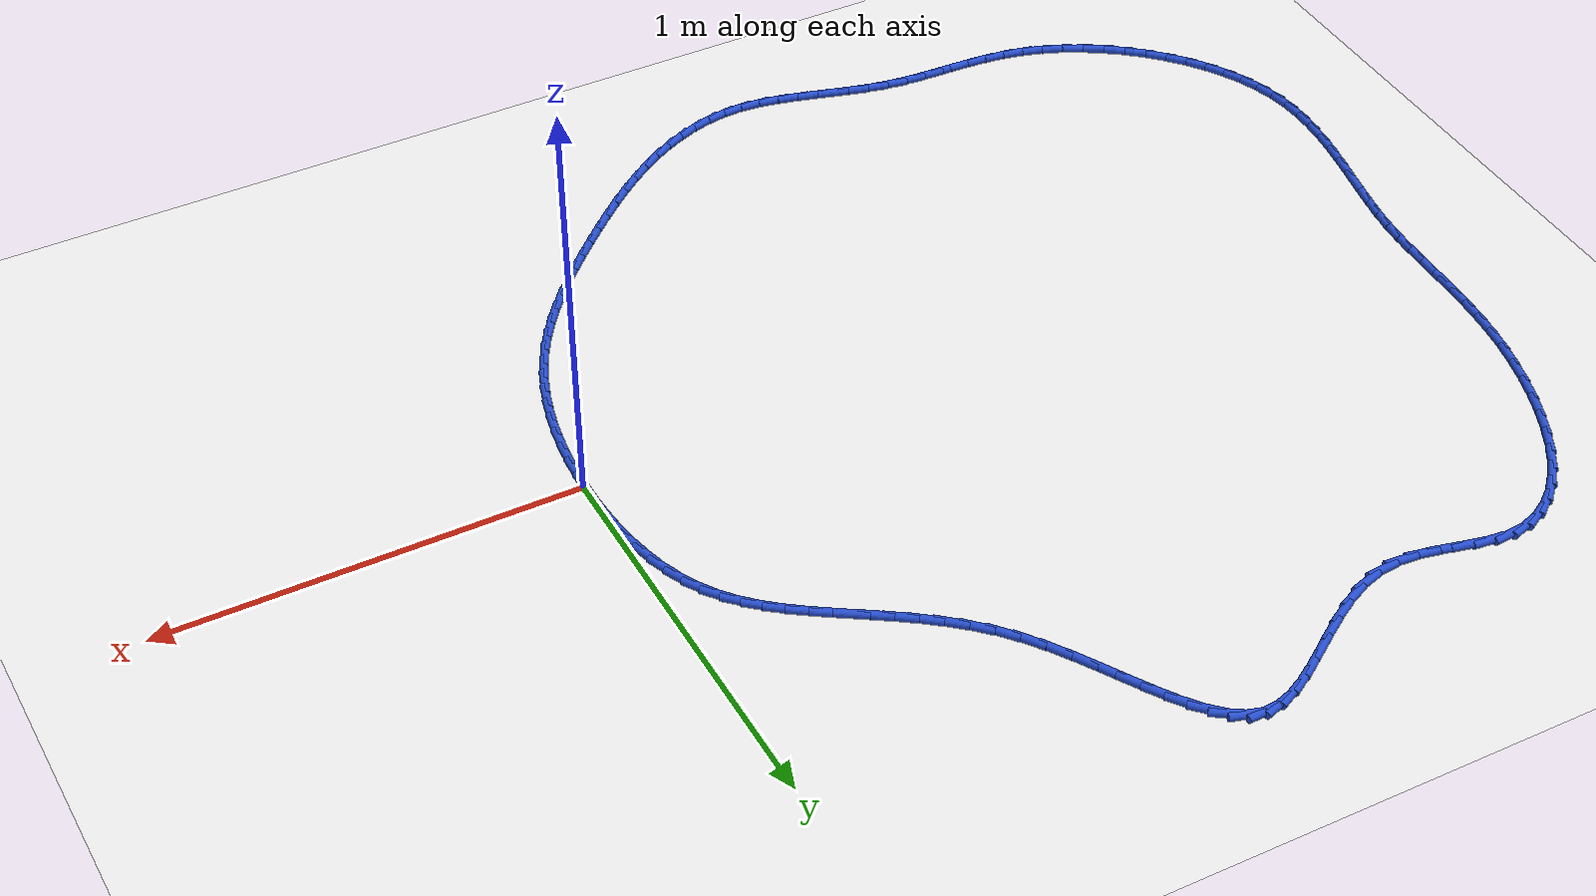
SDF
<sdf version="1.6">
 <world name="default">
  <light name="sun" type="directional">
   <pose>0 0 10 0 -0 0</pose>
   <diffuse>0.8 0.8 0.8 1</diffuse>
   <specular>0.2 0.2 0.2 1</specular>
   <attenuation>
    <range>1000</range>
    <constant>0.9</constant>
    <linear>0.01</linear>
    <quadratic>0.001</quadratic>
   </attenuation>
   <direction>-0.5 0.1 -0.9</direction>
  </light>
  <model name="ground_plane">
   <static>1</static>
   <link name="link">
    <collision name="collision">
     <geometry><plane><normal>0 0 1</normal><size>100 100</size></plane></geometry>
     <surface><friction><ode><mu>100</mu><mu2>50</mu2></ode></friction></surface>
    </collision>
    <visual name="visual">
     <cast_shadows>0</cast_shadows>
     <geometry><plane><normal>0 0 1</normal><size>100 100</size></plane></geometry>
     <material>
      <script><uri>file://media/materials/scripts/gazebo.material</uri><name>Gazebo/WhiteGlow</name></script>
     </material>
    </visual>
   </link>
  </model>
  <gravity>0 0 -9.8</gravity>
  <magnetic_field>6e-06 2.3e-05 -4.2e-05</magnetic_field>
  <atmosphere type="adiabatic"/>
  <physics name="default_physics" default="0" type="ode">
   <max_step_size>0.001</max_step_size>
   <real_time_factor>1</real_time_factor>
   <real_time_update_rate>1000</real_time_update_rate>
  </physics>
  <scene><ambient>0.4 0.4 0.4 1</ambient><background>0.7 0.7 0.7 1</background><shadows>1</shadows></scene>
  <spherical_coordinates>
   <surface_model>EARTH_WGS84</surface_model>
   <latitude_deg>0</latitude_deg>
   <longitude_deg>0</longitude_deg>
   <elevation>0</elevation>
   <heading_deg>0</heading_deg>
  </spherical_coordinates>
  <model name="line">
   <link name="link_0">
    <pose>-3.122502256758253e-17 -1.3877787807814457e-17 0.01 0 1.57 -1.5706837754737317</pose>
    <collision name="collision">
     <geometry><cylinder><radius>0.01</radius><length>0.08</length></cylinder></geometry>
    </collision>
    <visual name="visual">
     <material>
      <script><name>Gazebo/Blue</name><uri>file://media/materials/scripts/gazebo.material</uri></script>
     </material>
     <geometry><cylinder><radius>0.01</radius><length>0.08</length></cylinder></geometry>
    </visual>
   </link>
   <link name="link_1">
    <pose>-6.065359261570258e-06 0.05388972046839372 0.01 0 1.57 -1.5262894574556105</pose>
    <collision name="collision">
     <geometry><cylinder><radius>0.01</radius><length>0.08</length></cylinder></geometry>
    </collision>
    <visual name="visual">
     <material>
      <script><name>Gazebo/Blue</name><uri>file://media/materials/scripts/gazebo.material</uri></script>
     </material>
     <geometry><cylinder><radius>0.01</radius><length>0.08</length></cylinder></geometry>
    </visual>
   </link>
   <link name="link_2">
    <pose>-0.0024095332956994902 0.10785623807598792 0.01 0 1.57 -1.4769604596576116</pose>
    <collision name="collision">
     <geometry><cylinder><radius>0.01</radius><length>0.08</length></cylinder></geometry>
    </collision>
    <visual name="visual">
     <material>
      <script><name>Gazebo/Blue</name><uri>file://media/materials/scripts/gazebo.material</uri></script>
     </material>
     <geometry><cylinder><radius>0.01</radius><length>0.08</length></cylinder></geometry>
    </visual>
   </link>
   <link name="link_3">
    <pose>-0.0074465998001762915 0.16137813643352678 0.01 0 1.57 -1.4214694452902707</pose>
    <collision name="collision">
     <geometry><cylinder><radius>0.01</radius><length>0.08</length></cylinder></geometry>
    </collision>
    <visual name="visual">
     <material>
      <script><name>Gazebo/Blue</name><uri>file://media/materials/scripts/gazebo.material</uri></script>
     </material>
     <geometry><cylinder><radius>0.01</radius><length>0.08</length></cylinder></geometry>
    </visual>
   </link>
   <link name="link_4">
    <pose>-0.015353460863554455 0.21393399915175437 0.01 0 1.57 -1.3583999256860129</pose>
    <collision name="collision">
     <geometry><cylinder><radius>0.01</radius><length>0.08</length></cylinder></geometry>
    </collision>
    <visual name="visual">
     <material>
      <script><name>Gazebo/Blue</name><uri>file://media/materials/scripts/gazebo.material</uri></script>
     </material>
     <geometry><cylinder><radius>0.01</radius><length>0.08</length></cylinder></geometry>
    </visual>
   </link>
   <link name="link_5">
    <pose>-0.026366312476696505 0.26500240984141504 0.01 0 1.57 -1.2861382163552393</pose>
    <collision name="collision">
     <geometry><cylinder><radius>0.01</radius><length>0.08</length></cylinder></geometry>
    </collision>
    <visual name="visual">
     <material>
      <script><name>Gazebo/Blue</name><uri>file://media/materials/scripts/gazebo.material</uri></script>
     </material>
     <geometry><cylinder><radius>0.01</radius><length>0.08</length></cylinder></geometry>
    </visual>
   </link>
   <link name="link_6">
    <pose>-0.040721350630464934 0.3140619521132529 0.01 0 1.57 -1.2029196158675228</pose>
    <collision name="collision">
     <geometry><cylinder><radius>0.01</radius><length>0.08</length></cylinder></geometry>
    </collision>
    <visual name="visual">
     <material>
      <script><name>Gazebo/Blue</name><uri>file://media/materials/scripts/gazebo.material</uri></script>
     </material>
     <geometry><cylinder><radius>0.01</radius><length>0.08</length></cylinder></geometry>
    </visual>
   </link>
   <link name="link_7">
    <pose>-0.058654771315722214 0.36059120957801205 0.01 0 1.57 -1.1069790616883945</pose>
    <collision name="collision">
     <geometry><cylinder><radius>0.01</radius><length>0.08</length></cylinder></geometry>
    </collision>
    <visual name="visual">
     <material>
      <script><name>Gazebo/Blue</name><uri>file://media/materials/scripts/gazebo.material</uri></script>
     </material>
     <geometry><cylinder><radius>0.01</radius><length>0.08</length></cylinder></geometry>
    </visual>
   </link>
   <link name="link_8">
    <pose>-0.08040277052333086 0.4040687658464368 0.01 0 1.57 -0.996958390001971</pose>
    <collision name="collision">
     <geometry><cylinder><radius>0.01</radius><length>0.08</length></cylinder></geometry>
    </collision>
    <visual name="visual">
     <material>
      <script><name>Gazebo/Blue</name><uri>file://media/materials/scripts/gazebo.material</uri></script>
     </material>
     <geometry><cylinder><radius>0.01</radius><length>0.08</length></cylinder></geometry>
    </visual>
   </link>
   <link name="link_9">
    <pose>-0.10619921828798255 0.44397684366696755 0.01 0 1.57 -0.8817575596938176</pose>
    <collision name="collision">
     <geometry><cylinder><radius>0.01</radius><length>0.08</length></cylinder></geometry>
    </collision>
    <visual name="visual">
     <material>
      <script><name>Gazebo/Blue</name><uri>file://media/materials/scripts/gazebo.material</uri></script>
     </material>
     <geometry><cylinder><radius>0.01</radius><length>0.08</length></cylinder></geometry>
    </visual>
   </link>
   <link name="link_10">
    <pose>-0.13602789926728126 0.4801889436351819 0.01 0 1.57 -0.7816309510672206</pose>
    <collision name="collision">
     <geometry><cylinder><radius>0.01</radius><length>0.08</length></cylinder></geometry>
    </collision>
    <visual name="visual">
     <material>
      <script><name>Gazebo/Blue</name><uri>file://media/materials/scripts/gazebo.material</uri></script>
     </material>
     <geometry><cylinder><radius>0.01</radius><length>0.08</length></cylinder></geometry>
    </visual>
   </link>
   <link name="link_11">
    <pose>-0.1694029077207042 0.5133134331746986 0.01 0 1.57 -0.7012972215751669</pose>
    <collision name="collision">
     <geometry><cylinder><radius>0.01</radius><length>0.08</length></cylinder></geometry>
    </collision>
    <visual name="visual">
     <material>
      <script><name>Gazebo/Blue</name><uri>file://media/materials/scripts/gazebo.material</uri></script>
     </material>
     <geometry><cylinder><radius>0.01</radius><length>0.08</length></cylinder></geometry>
    </visual>
   </link>
   <link name="link_12">
    <pose>-0.20578654305830904 0.5440397167430072 0.01 0 1.57 -0.6414647554955005</pose>
    <collision name="collision">
     <geometry><cylinder><radius>0.01</radius><length>0.08</length></cylinder></geometry>
    </collision>
    <visual name="visual">
     <material>
      <script><name>Gazebo/Blue</name><uri>file://media/materials/scripts/gazebo.material</uri></script>
     </material>
     <geometry><cylinder><radius>0.01</radius><length>0.08</length></cylinder></geometry>
    </visual>
   </link>
   <link name="link_13">
    <pose>-0.24464110469015338 0.5730571987975979 0.01 0 1.57 -0.601562473619099</pose>
    <collision name="collision">
     <geometry><cylinder><radius>0.01</radius><length>0.08</length></cylinder></geometry>
    </collision>
    <visual name="visual">
     <material>
      <script><name>Gazebo/Blue</name><uri>file://media/materials/scripts/gazebo.material</uri></script>
     </material>
     <geometry><cylinder><radius>0.01</radius><length>0.08</length></cylinder></geometry>
    </visual>
   </link>
   <link name="link_14">
    <pose>-0.2854288920262947 0.6010552837959603 0.01 0 1.57 -0.580512630095227</pose>
    <collision name="collision">
     <geometry><cylinder><radius>0.01</radius><length>0.08</length></cylinder></geometry>
    </collision>
    <visual name="visual">
     <material>
      <script><name>Gazebo/Blue</name><uri>file://media/materials/scripts/gazebo.material</uri></script>
     </material>
     <geometry><cylinder><radius>0.01</radius><length>0.08</length></cylinder></geometry>
    </visual>
   </link>
   <link name="link_15">
    <pose>-0.3276122044767906 0.6287233761955842 0.01 0 1.57 -0.5772039184290051</pose>
    <collision name="collision">
     <geometry><cylinder><radius>0.01</radius><length>0.08</length></cylinder></geometry>
    </collision>
    <visual name="visual">
     <material>
      <script><name>Gazebo/Blue</name><uri>file://media/materials/scripts/gazebo.material</uri></script>
     </material>
     <geometry><cylinder><radius>0.01</radius><length>0.08</length></cylinder></geometry>
    </visual>
   </link>
   <link name="link_16">
    <pose>-0.3706533414516988 0.6567508804539598 0.01 0 1.57 -0.5906930429041665</pose>
    <collision name="collision">
     <geometry><cylinder><radius>0.01</radius><length>0.08</length></cylinder></geometry>
    </collision>
    <visual name="visual">
     <material>
      <script><name>Gazebo/Blue</name><uri>file://media/materials/scripts/gazebo.material</uri></script>
     </material>
     <geometry><cylinder><radius>0.01</radius><length>0.08</length></cylinder></geometry>
    </visual>
   </link>
   <link name="link_17">
    <pose>-0.41401460236107673 0.6858272010285766 0.01 0 1.57 -0.6202130189465316</pose>
    <collision name="collision">
     <geometry><cylinder><radius>0.01</radius><length>0.08</length></cylinder></geometry>
    </collision>
    <visual name="visual">
     <material>
      <script><name>Gazebo/Blue</name><uri>file://media/materials/scripts/gazebo.material</uri></script>
     </material>
     <geometry><cylinder><radius>0.01</radius><length>0.08</length></cylinder></geometry>
    </visual>
   </link>
   <link name="link_18">
    <pose>-0.45715828661498203 0.7166417423769246 0.01 0 1.57 -0.6650494758078626</pose>
    <collision name="collision">
     <geometry><cylinder><radius>0.01</radius><length>0.08</length></cylinder></geometry>
    </collision>
    <visual name="visual">
     <material>
      <script><name>Gazebo/Blue</name><uri>file://media/materials/scripts/gazebo.material</uri></script>
     </material>
     <geometry><cylinder><radius>0.01</radius><length>0.08</length></cylinder></geometry>
    </visual>
   </link>
   <link name="link_19">
    <pose>-0.4995466936234724 0.7498839089564937 0.01 0 1.57 -0.7243257233090041</pose>
    <collision name="collision">
     <geometry><cylinder><radius>0.01</radius><length>0.08</length></cylinder></geometry>
    </collision>
    <visual name="visual">
     <material>
      <script><name>Gazebo/Blue</name><uri>file://media/materials/scripts/gazebo.material</uri></script>
     </material>
     <geometry><cylinder><radius>0.01</radius><length>0.08</length></cylinder></geometry>
    </visual>
   </link>
   <link name="link_20">
    <pose>-0.5406421227966053 0.7862431052247737 0.01 0 1.57 -0.796739428894704</pose>
    <collision name="collision">
     <geometry><cylinder><radius>0.01</radius><length>0.08</length></cylinder></geometry>
    </collision>
    <visual name="visual">
     <material>
      <script><name>Gazebo/Blue</name><uri>file://media/materials/scripts/gazebo.material</uri></script>
     </material>
     <geometry><cylinder><radius>0.01</radius><length>0.08</length></cylinder></geometry>
    </visual>
   </link>
   <link name="link_21">
    <pose>-0.5799068735444384 0.8264087356392544 0.01 0 1.57 -0.8800578718668401</pose>
    <collision name="collision">
     <geometry><cylinder><radius>0.01</radius><length>0.08</length></cylinder></geometry>
    </collision>
    <visual name="visual">
     <material>
      <script><name>Gazebo/Blue</name><uri>file://media/materials/scripts/gazebo.material</uri></script>
     </material>
     <geometry><cylinder><radius>0.01</radius><length>0.08</length></cylinder></geometry>
    </visual>
   </link>
   <link name="link_22">
    <pose>-0.6168100834937159 0.8710544857775265 0.01 0 1.57 -0.9576282131948122</pose>
    <collision name="collision">
     <geometry><cylinder><radius>0.01</radius><length>0.08</length></cylinder></geometry>
    </collision>
    <visual name="visual">
     <material>
      <script><name>Gazebo/Blue</name><uri>file://media/materials/scripts/gazebo.material</uri></script>
     </material>
     <geometry><cylinder><radius>0.01</radius><length>0.08</length></cylinder></geometry>
    </visual>
   </link>
   <link name="link_23">
    <pose>-0.6512145563338 0.9199491284538198 0.01 0 1.57 -1.009935038923003</pose>
    <collision name="collision">
     <geometry><cylinder><radius>0.01</radius><length>0.08</length></cylinder></geometry>
    </collision>
    <visual name="visual">
     <material>
      <script><name>Gazebo/Blue</name><uri>file://media/materials/scripts/gazebo.material</uri></script>
     </material>
     <geometry><cylinder><radius>0.01</radius><length>0.08</length></cylinder></geometry>
    </visual>
   </link>
   <link name="link_24">
    <pose>-0.6835839049696123 0.9714803676549154 0.01 0 1.57 -1.039046206031808</pose>
    <collision name="collision">
     <geometry><cylinder><radius>0.01</radius><length>0.08</length></cylinder></geometry>
    </collision>
    <visual name="visual">
     <material>
      <script><name>Gazebo/Blue</name><uri>file://media/materials/scripts/gazebo.material</uri></script>
     </material>
     <geometry><cylinder><radius>0.01</radius><length>0.08</length></cylinder></geometry>
    </visual>
   </link>
   <link name="link_25">
    <pose>-0.7144323446235916 1.0239195887734225 0.01 0 1.57 -1.0466203358452024</pose>
    <collision name="collision">
     <geometry><cylinder><radius>0.01</radius><length>0.08</length></cylinder></geometry>
    </collision>
    <visual name="visual">
     <material>
      <script><name>Gazebo/Blue</name><uri>file://media/materials/scripts/gazebo.material</uri></script>
     </material>
     <geometry><cylinder><radius>0.01</radius><length>0.08</length></cylinder></geometry>
    </visual>
   </link>
   <link name="link_26">
    <pose>-0.7442740905181762 1.0755381772019499 0.01 0 1.57 -1.0317616313111426</pose>
    <collision name="collision">
     <geometry><cylinder><radius>0.01</radius><length>0.08</length></cylinder></geometry>
    </collision>
    <visual name="visual">
     <material>
      <script><name>Gazebo/Blue</name><uri>file://media/materials/scripts/gazebo.material</uri></script>
     </material>
     <geometry><cylinder><radius>0.01</radius><length>0.08</length></cylinder></geometry>
    </visual>
   </link>
   <link name="link_27">
    <pose>-0.7736233578758047 1.124607518333107 0.01 0 1.57 -0.9904052859496894</pose>
    <collision name="collision">
     <geometry><cylinder><radius>0.01</radius><length>0.08</length></cylinder></geometry>
    </collision>
    <visual name="visual">
     <material>
      <script><name>Gazebo/Blue</name><uri>file://media/materials/scripts/gazebo.material</uri></script>
     </material>
     <geometry><cylinder><radius>0.01</radius><length>0.08</length></cylinder></geometry>
    </visual>
   </link>
   <link name="link_28">
    <pose>-0.8029943619189166 1.1693989975595038 0.01 0 1.57 -0.9139299928060335</pose>
    <collision name="collision">
     <geometry><cylinder><radius>0.01</radius><length>0.08</length></cylinder></geometry>
    </collision>
    <visual name="visual">
     <material>
      <script><name>Gazebo/Blue</name><uri>file://media/materials/scripts/gazebo.material</uri></script>
     </material>
     <geometry><cylinder><radius>0.01</radius><length>0.08</length></cylinder></geometry>
    </visual>
   </link>
   <link name="link_29">
    <pose>-0.8329013178699499 1.208184000273749 0.01 0 1.57 -0.7868945814173393</pose>
    <collision name="collision">
     <geometry><cylinder><radius>0.01</radius><length>0.08</length></cylinder></geometry>
    </collision>
    <visual name="visual">
     <material>
      <script><name>Gazebo/Blue</name><uri>file://media/materials/scripts/gazebo.material</uri></script>
     </material>
     <geometry><cylinder><radius>0.01</radius><length>0.08</length></cylinder></geometry>
    </visual>
   </link>
   <link name="link_30">
    <pose>-0.8638584409513439 1.2392339118684517 0.01 0 1.57 -0.5859818625668931</pose>
    <collision name="collision">
     <geometry><cylinder><radius>0.01</radius><length>0.08</length></cylinder></geometry>
    </collision>
    <visual name="visual">
     <material>
      <script><name>Gazebo/Blue</name><uri>file://media/materials/scripts/gazebo.material</uri></script>
     </material>
     <geometry><cylinder><radius>0.01</radius><length>0.08</length></cylinder></geometry>
    </visual>
   </link>
   <link name="link_31">
    <pose>-0.8963799463855368 1.260820117736221 0.01 0 1.57 -0.29182411329928054</pose>
    <collision name="collision">
     <geometry><cylinder><radius>0.01</radius><length>0.08</length></cylinder></geometry>
    </collision>
    <visual name="visual">
     <material>
      <script><name>Gazebo/Blue</name><uri>file://media/materials/scripts/gazebo.material</uri></script>
     </material>
     <geometry><cylinder><radius>0.01</radius><length>0.08</length></cylinder></geometry>
    </visual>
   </link>
   <link name="link_32">
    <pose>-0.9309800493949676 1.2712140032696668 0.01 0 1.57 0.053700631312974124</pose>
    <collision name="collision">
     <geometry><cylinder><radius>0.01</radius><length>0.08</length></cylinder></geometry>
    </collision>
    <visual name="visual">
     <material>
      <script><name>Gazebo/Blue</name><uri>file://media/materials/scripts/gazebo.material</uri></script>
     </material>
     <geometry><cylinder><radius>0.01</radius><length>0.08</length></cylinder></geometry>
    </visual>
   </link>
   <link name="link_33">
    <pose>-0.9680781363720831 1.2692198953684701 0.01 0 1.57 0.3148752583680107</pose>
    <collision name="collision">
     <geometry><cylinder><radius>0.01</radius><length>0.08</length></cylinder></geometry>
    </collision>
    <visual name="visual">
     <material>
      <script><name>Gazebo/Blue</name><uri>file://media/materials/scripts/gazebo.material</uri></script>
     </material>
     <geometry><cylinder><radius>0.01</radius><length>0.08</length></cylinder></geometry>
    </visual>
   </link>
   <link name="link_34">
    <pose>-1.0076130260902345 1.2563429286001233 0.01 0 1.57 0.4735951893861203</pose>
    <collision name="collision">
     <geometry><cylinder><radius>0.01</radius><length>0.08</length></cylinder></geometry>
    </collision>
    <visual name="visual">
     <material>
      <script><name>Gazebo/Blue</name><uri>file://media/materials/scripts/gazebo.material</uri></script>
     </material>
     <geometry><cylinder><radius>0.01</radius><length>0.08</length></cylinder></geometry>
    </visual>
   </link>
   <link name="link_35">
    <pose>-1.0493716681372567 1.2349417479320077 0.01 0 1.57 0.5620521152027576</pose>
    <collision name="collision">
     <geometry><cylinder><radius>0.01</radius><length>0.08</length></cylinder></geometry>
    </collision>
    <visual name="visual">
     <material>
      <script><name>Gazebo/Blue</name><uri>file://media/materials/scripts/gazebo.material</uri></script>
     </material>
     <geometry><cylinder><radius>0.01</radius><length>0.08</length></cylinder></geometry>
    </visual>
   </link>
   <link name="link_36">
    <pose>-1.0931409532675855 1.2073753289773634 0.01 0 1.57 0.602964983971125</pose>
    <collision name="collision">
     <geometry><cylinder><radius>0.01</radius><length>0.08</length></cylinder></geometry>
    </collision>
    <visual name="visual">
     <material>
      <script><name>Gazebo/Blue</name><uri>file://media/materials/scripts/gazebo.material</uri></script>
     </material>
     <geometry><cylinder><radius>0.01</radius><length>0.08</length></cylinder></geometry>
    </visual>
   </link>
   <link name="link_37">
    <pose>-1.1387077722356573 1.1760026473494305 0.01 0 1.57 0.6080749728579141</pose>
    <collision name="collision">
     <geometry><cylinder><radius>0.01</radius><length>0.08</length></cylinder></geometry>
    </collision>
    <visual name="visual">
     <material>
      <script><name>Gazebo/Blue</name><uri>file://media/materials/scripts/gazebo.material</uri></script>
     </material>
     <geometry><cylinder><radius>0.01</radius><length>0.08</length></cylinder></geometry>
    </visual>
   </link>
   <link name="link_38">
    <pose>-1.1858590157959077 1.143182678661449 0.01 0 1.57 0.5816971627424746</pose>
    <collision name="collision">
     <geometry><cylinder><radius>0.01</radius><length>0.08</length></cylinder></geometry>
    </collision>
    <visual name="visual">
     <material>
      <script><name>Gazebo/Blue</name><uri>file://media/materials/scripts/gazebo.material</uri></script>
     </material>
     <geometry><cylinder><radius>0.01</radius><length>0.08</length></cylinder></geometry>
    </visual>
   </link>
   <link name="link_39">
    <pose>-1.2343815747027735 1.1112743985266587 0.01 0 1.57 0.5229103019647605</pose>
    <collision name="collision">
     <geometry><cylinder><radius>0.01</radius><length>0.08</length></cylinder></geometry>
    </collision>
    <visual name="visual">
     <material>
      <script><name>Gazebo/Blue</name><uri>file://media/materials/scripts/gazebo.material</uri></script>
     </material>
     <geometry><cylinder><radius>0.01</radius><length>0.08</length></cylinder></geometry>
    </visual>
   </link>
   <link name="link_40">
    <pose>-1.2840623397106905 1.0826367825583005 0.01 0 1.57 0.4265656241966764</pose>
    <collision name="collision">
     <geometry><cylinder><radius>0.01</radius><length>0.08</length></cylinder></geometry>
    </collision>
    <visual name="visual">
     <material>
      <script><name>Gazebo/Blue</name><uri>file://media/materials/scripts/gazebo.material</uri></script>
     </material>
     <geometry><cylinder><radius>0.01</radius><length>0.08</length></cylinder></geometry>
    </visual>
   </link>
   <link name="link_41">
    <pose>-1.3346882015740955 1.0596288063696138 0.01 0 1.57 0.28451153124987966</pose>
    <collision name="collision">
     <geometry><cylinder><radius>0.01</radius><length>0.08</length></cylinder></geometry>
    </collision>
    <visual name="visual">
     <material>
      <script><name>Gazebo/Blue</name><uri>file://media/materials/scripts/gazebo.material</uri></script>
     </material>
     <geometry><cylinder><radius>0.01</radius><length>0.08</length></cylinder></geometry>
    </visual>
   </link>
   <link name="link_42">
    <pose>-1.386046051047423 1.044609445573839 0.01 0 1.57 0.09186251432882939</pose>
    <collision name="collision">
     <geometry><cylinder><radius>0.01</radius><length>0.08</length></cylinder></geometry>
    </collision>
    <visual name="visual">
     <material>
      <script><name>Gazebo/Blue</name><uri>file://media/materials/scripts/gazebo.material</uri></script>
     </material>
     <geometry><cylinder><radius>0.01</radius><length>0.08</length></cylinder></geometry>
    </visual>
   </link>
   <link name="link_43">
    <pose>-1.437917853046733 1.0398309223089708 0.01 0 1.57 -0.09280384876174592</pose>
    <collision name="collision">
     <geometry><cylinder><radius>0.01</radius><length>0.08</length></cylinder></geometry>
    </collision>
    <visual name="visual">
     <material>
      <script><name>Gazebo/Blue</name><uri>file://media/materials/scripts/gazebo.material</uri></script>
     </material>
     <geometry><cylinder><radius>0.01</radius><length>0.08</length></cylinder></geometry>
    </visual>
   </link>
   <link name="link_44">
    <pose>-1.4899530726125396 1.0446739024218281 0.01 0 1.57 -0.20446269059833902</pose>
    <collision name="collision">
     <geometry><cylinder><radius>0.01</radius><length>0.08</length></cylinder></geometry>
    </collision>
    <visual name="visual">
     <material>
      <script><name>Gazebo/Blue</name><uri>file://media/materials/scripts/gazebo.material</uri></script>
     </material>
     <geometry><cylinder><radius>0.01</radius><length>0.08</length></cylinder></geometry>
    </visual>
   </link>
   <link name="link_45">
    <pose>-1.541657035934609 1.055395253929441 0.01 0 1.57 -0.24463790247810926</pose>
    <collision name="collision">
     <geometry><cylinder><radius>0.01</radius><length>0.08</length></cylinder></geometry>
    </collision>
    <visual name="visual">
     <material>
      <script><name>Gazebo/Blue</name><uri>file://media/materials/scripts/gazebo.material</uri></script>
     </material>
     <geometry><cylinder><radius>0.01</radius><length>0.08</length></cylinder></geometry>
    </visual>
   </link>
   <link name="link_46">
    <pose>-1.592527810395201 1.0680945309323007 0.01 0 1.57 -0.21421751918496046</pose>
    <collision name="collision">
     <geometry><cylinder><radius>0.01</radius><length>0.08</length></cylinder></geometry>
    </collision>
    <visual name="visual">
     <material>
      <script><name>Gazebo/Blue</name><uri>file://media/materials/scripts/gazebo.material</uri></script>
     </material>
     <geometry><cylinder><radius>0.01</radius><length>0.08</length></cylinder></geometry>
    </visual>
   </link>
   <link name="link_47">
    <pose>-1.6420634633765747 1.0788712875308992 0.01 0 1.57 -0.10348509432377698</pose>
    <collision name="collision">
     <geometry><cylinder><radius>0.01</radius><length>0.08</length></cylinder></geometry>
    </collision>
    <visual name="visual">
     <material>
      <script><name>Gazebo/Blue</name><uri>file://media/materials/scripts/gazebo.material</uri></script>
     </material>
     <geometry><cylinder><radius>0.01</radius><length>0.08</length></cylinder></geometry>
    </visual>
   </link>
   <link name="link_48">
    <pose>-1.689762062260991 1.0838250778257286 0.01 0 1.57 0.09554567706389125</pose>
    <collision name="collision">
     <geometry><cylinder><radius>0.01</radius><length>0.08</length></cylinder></geometry>
    </collision>
    <visual name="visual">
     <material>
      <script><name>Gazebo/Blue</name><uri>file://media/materials/scripts/gazebo.material</uri></script>
     </material>
     <geometry><cylinder><radius>0.01</radius><length>0.08</length></cylinder></geometry>
    </visual>
   </link>
   <link name="link_49">
    <pose>-1.7351596189251437 1.0794742900597543 0.01 0 1.57 0.3166772505488083</pose>
    <collision name="collision">
     <geometry><cylinder><radius>0.01</radius><length>0.08</length></cylinder></geometry>
    </collision>
    <visual name="visual">
     <material>
      <script><name>Gazebo/Blue</name><uri>file://media/materials/scripts/gazebo.material</uri></script>
     </material>
     <geometry><cylinder><radius>0.01</radius><length>0.08</length></cylinder></geometry>
    </visual>
   </link>
   <link name="link_50">
    <pose>-1.7780707052359586 1.0654120782982632 0.01 0 1.57 0.5143831275963655</pose>
    <collision name="collision">
     <geometry><cylinder><radius>0.01</radius><length>0.08</length></cylinder></geometry>
    </collision>
    <visual name="visual">
     <material>
      <script><name>Gazebo/Blue</name><uri>file://media/materials/scripts/gazebo.material</uri></script>
     </material>
     <geometry><cylinder><radius>0.01</radius><length>0.08</length></cylinder></geometry>
    </visual>
   </link>
   <link name="link_51">
    <pose>-1.8184340151005531 1.0426016648875729 0.01 0 1.57 0.6809322049603105</pose>
    <collision name="collision">
     <geometry><cylinder><radius>0.01</radius><length>0.08</length></cylinder></geometry>
    </collision>
    <visual name="visual">
     <material>
      <script><name>Gazebo/Blue</name><uri>file://media/materials/scripts/gazebo.material</uri></script>
     </material>
     <geometry><cylinder><radius>0.01</radius><length>0.08</length></cylinder></geometry>
    </visual>
   </link>
   <link name="link_52">
    <pose>-1.8561888124455113 1.01201256409113 0.01 0 1.57 0.817294119532984</pose>
    <collision name="collision">
     <geometry><cylinder><radius>0.01</radius><length>0.08</length></cylinder></geometry>
    </collision>
    <visual name="visual">
     <material>
      <script><name>Gazebo/Blue</name><uri>file://media/materials/scripts/gazebo.material</uri></script>
     </material>
     <geometry><cylinder><radius>0.01</radius><length>0.08</length></cylinder></geometry>
    </visual>
   </link>
   <link name="link_53">
    <pose>-1.8912743611974165 0.9746142901723824 0.01 0 1.57 0.9283749290603787</pose>
    <collision name="collision">
     <geometry><cylinder><radius>0.01</radius><length>0.08</length></cylinder></geometry>
    </collision>
    <visual name="visual">
     <material>
      <script><name>Gazebo/Blue</name><uri>file://media/materials/scripts/gazebo.material</uri></script>
     </material>
     <geometry><cylinder><radius>0.01</radius><length>0.08</length></cylinder></geometry>
    </visual>
   </link>
   <link name="link_54">
    <pose>-1.9236299252828528 0.9313763573947772 0.01 0 1.57 1.019746566510972</pose>
    <collision name="collision">
     <geometry><cylinder><radius>0.01</radius><length>0.08</length></cylinder></geometry>
    </collision>
    <visual name="visual">
     <material>
      <script><name>Gazebo/Blue</name><uri>file://media/materials/scripts/gazebo.material</uri></script>
     </material>
     <geometry><cylinder><radius>0.01</radius><length>0.08</length></cylinder></geometry>
    </visual>
   </link>
   <link name="link_55">
    <pose>-1.9531947686284052 0.8832682800217616 0.01 0 1.57 1.0963019263351506</pose>
    <collision name="collision">
     <geometry><cylinder><radius>0.01</radius><length>0.08</length></cylinder></geometry>
    </collision>
    <visual name="visual">
     <material>
      <script><name>Gazebo/Blue</name><uri>file://media/materials/scripts/gazebo.material</uri></script>
     </material>
     <geometry><cylinder><radius>0.01</radius><length>0.08</length></cylinder></geometry>
    </visual>
   </link>
   <link name="link_56">
    <pose>-1.9799081551606559 0.8312595723167838 0.01 0 1.57 1.161981417101356</pose>
    <collision name="collision">
     <geometry><cylinder><radius>0.01</radius><length>0.08</length></cylinder></geometry>
    </collision>
    <visual name="visual">
     <material>
      <script><name>Gazebo/Blue</name><uri>file://media/materials/scripts/gazebo.material</uri></script>
     </material>
     <geometry><cylinder><radius>0.01</radius><length>0.08</length></cylinder></geometry>
    </visual>
   </link>
   <link name="link_57">
    <pose>-2.00370934880619 0.77631974854329 0.01 0 1.57 1.2199030079689364</pose>
    <collision name="collision">
     <geometry><cylinder><radius>0.01</radius><length>0.08</length></cylinder></geometry>
    </collision>
    <visual name="visual">
     <material>
      <script><name>Gazebo/Blue</name><uri>file://media/materials/scripts/gazebo.material</uri></script>
     </material>
     <geometry><cylinder><radius>0.01</radius><length>0.08</length></cylinder></geometry>
    </visual>
   </link>
   <link name="link_58">
    <pose>-2.0245376134915904 0.7194183229647289 0.01 0 1.57 1.272593897706896</pose>
    <collision name="collision">
     <geometry><cylinder><radius>0.01</radius><length>0.08</length></cylinder></geometry>
    </collision>
    <visual name="visual">
     <material>
      <script><name>Gazebo/Blue</name><uri>file://media/materials/scripts/gazebo.material</uri></script>
     </material>
     <geometry><cylinder><radius>0.01</radius><length>0.08</length></cylinder></geometry>
    </visual>
   </link>
   <link name="link_59">
    <pose>-2.0423322131434425 0.6615248098445469 0.01 0 1.57 1.3222266275416488</pose>
    <collision name="collision">
     <geometry><cylinder><radius>0.01</radius><length>0.08</length></cylinder></geometry>
    </collision>
    <visual name="visual">
     <material>
      <script><name>Gazebo/Blue</name><uri>file://media/materials/scripts/gazebo.material</uri></script>
     </material>
     <geometry><cylinder><radius>0.01</radius><length>0.08</length></cylinder></geometry>
    </visual>
   </link>
   <link name="link_60">
    <pose>-2.057032411688329 0.6036087234461924 0.01 0 1.57 1.3708495413388049</pose>
    <collision name="collision">
     <geometry><cylinder><radius>0.01</radius><length>0.08</length></cylinder></geometry>
    </collision>
    <visual name="visual">
     <material>
      <script><name>Gazebo/Blue</name><uri>file://media/materials/scripts/gazebo.material</uri></script>
     </material>
     <geometry><cylinder><radius>0.01</radius><length>0.08</length></cylinder></geometry>
    </visual>
   </link>
   <link name="link_61">
    <pose>-2.068577473052834 0.5466395780331116 0.01 0 1.57 1.4193669720137025</pose>
    <collision name="collision">
     <geometry><cylinder><radius>0.01</radius><length>0.08</length></cylinder></geometry>
    </collision>
    <visual name="visual">
     <material>
      <script><name>Gazebo/Blue</name><uri>file://media/materials/scripts/gazebo.material</uri></script>
     </material>
     <geometry><cylinder><radius>0.01</radius><length>0.08</length></cylinder></geometry>
    </visual>
   </link>
   <link name="link_62">
    <pose>-2.077007962486158 0.49139301575579536 0.01 0 1.57 1.4632289868524422</pose>
    <collision name="collision">
     <geometry><cylinder><radius>0.01</radius><length>0.08</length></cylinder></geometry>
    </collision>
    <visual name="visual">
     <material>
      <script><name>Gazebo/Blue</name><uri>file://media/materials/scripts/gazebo.material</uri></script>
     </material>
     <geometry><cylinder><radius>0.01</radius><length>0.08</length></cylinder></geometry>
    </visual>
   </link>
   <link name="link_63">
    <pose>-2.0827923855760755 0.4378256796093578 0.01 0 1.57 1.4995840490043064</pose>
    <collision name="collision">
     <geometry><cylinder><radius>0.01</radius><length>0.08</length></cylinder></geometry>
    </collision>
    <visual name="visual">
     <material>
      <script><name>Gazebo/Blue</name><uri>file://media/materials/scripts/gazebo.material</uri></script>
     </material>
     <geometry><cylinder><radius>0.01</radius><length>0.08</length></cylinder></geometry>
    </visual>
   </link>
   <link name="link_64">
    <pose>-2.086512232068594 0.3856779816758233 0.01 0 1.57 1.5269557666267075</pose>
    <collision name="collision">
     <geometry><cylinder><radius>0.01</radius><length>0.08</length></cylinder></geometry>
    </collision>
    <visual name="visual">
     <material>
      <script><name>Gazebo/Blue</name><uri>file://media/materials/scripts/gazebo.material</uri></script>
     </material>
     <geometry><cylinder><radius>0.01</radius><length>0.08</length></cylinder></geometry>
    </visual>
   </link>
   <link name="link_65">
    <pose>-2.0887489923542755 0.3346903328036524 0.01 0 1.57 1.5441458322790114</pose>
    <collision name="collision">
     <geometry><cylinder><radius>0.01</radius><length>0.08</length></cylinder></geometry>
    </collision>
    <visual name="visual">
     <material>
      <script><name>Gazebo/Blue</name><uri>file://media/materials/scripts/gazebo.material</uri></script>
     </material>
     <geometry><cylinder><radius>0.01</radius><length>0.08</length></cylinder></geometry>
    </visual>
   </link>
   <link name="link_66">
    <pose>-2.0900841568236808 0.28460314384130564 0.01 0 1.57 1.5502707036945624</pose>
    <collision name="collision">
     <geometry><cylinder><radius>0.01</radius><length>0.08</length></cylinder></geometry>
    </collision>
    <visual name="visual">
     <material>
      <script><name>Gazebo/Blue</name><uri>file://media/materials/scripts/gazebo.material</uri></script>
     </material>
     <geometry><cylinder><radius>0.01</radius><length>0.08</length></cylinder></geometry>
    </visual>
   </link>
   <link name="link_67">
    <pose>-2.0910992158673727 0.2351568256372449 0.01 0 1.57 1.544786845321721</pose>
    <collision name="collision">
     <geometry><cylinder><radius>0.01</radius><length>0.08</length></cylinder></geometry>
    </collision>
    <visual name="visual">
     <material>
      <script><name>Gazebo/Blue</name><uri>file://media/materials/scripts/gazebo.material</uri></script>
     </material>
     <geometry><cylinder><radius>0.01</radius><length>0.08</length></cylinder></geometry>
    </visual>
   </link>
   <link name="link_68">
    <pose>-2.0923756598759127 0.18609178903993043 0.01 0 1.57 1.527521877497244</pose>
    <collision name="collision">
     <geometry><cylinder><radius>0.01</radius><length>0.08</length></cylinder></geometry>
    </collision>
    <visual name="visual">
     <material>
      <script><name>Gazebo/Blue</name><uri>file://media/materials/scripts/gazebo.material</uri></script>
     </material>
     <geometry><cylinder><radius>0.01</radius><length>0.08</length></cylinder></geometry>
    </visual>
   </link>
   <link name="link_69">
    <pose>-2.0944949792398617 0.1371484448978238 0.01 0 1.57 1.4987209958708538</pose>
    <collision name="collision">
     <geometry><cylinder><radius>0.01</radius><length>0.08</length></cylinder></geometry>
    </collision>
    <visual name="visual">
     <material>
      <script><name>Gazebo/Blue</name><uri>file://media/materials/scripts/gazebo.material</uri></script>
     </material>
     <geometry><cylinder><radius>0.01</radius><length>0.08</length></cylinder></geometry>
    </visual>
   </link>
   <link name="link_70">
    <pose>-2.0980386643497835 0.08806720405938544 0.01 0 1.57 1.4591361083514869</pose>
    <collision name="collision">
     <geometry><cylinder><radius>0.01</radius><length>0.08</length></cylinder></geometry>
    </collision>
    <visual name="visual">
     <material>
      <script><name>Gazebo/Blue</name><uri>file://media/materials/scripts/gazebo.material</uri></script>
     </material>
     <geometry><cylinder><radius>0.01</radius><length>0.08</length></cylinder></geometry>
    </visual>
   </link>
   <link name="link_71">
    <pose>-2.1035864912364945 0.03858896552915996 0.01 0 1.57 1.4168421263461002</pose>
    <collision name="collision">
     <geometry><cylinder><radius>0.01</radius><length>0.08</length></cylinder></geometry>
    </collision>
    <visual name="visual">
     <material>
      <script><name>Gazebo/Blue</name><uri>file://media/materials/scripts/gazebo.material</uri></script>
     </material>
     <geometry><cylinder><radius>0.01</radius><length>0.08</length></cylinder></geometry>
    </visual>
   </link>
   <link name="link_72">
    <pose>-2.111350183671395 -0.011440570493667184 0.01 0 1.57 1.3873818870089185</pose>
    <collision name="collision">
     <geometry><cylinder><radius>0.01</radius><length>0.08</length></cylinder></geometry>
    </collision>
    <visual name="visual">
     <material>
      <script><name>Gazebo/Blue</name><uri>file://media/materials/scripts/gazebo.material</uri></script>
     </material>
     <geometry><cylinder><radius>0.01</radius><length>0.08</length></cylinder></geometry>
    </visual>
   </link>
   <link name="link_73">
    <pose>-2.120718017666238 -0.06194123083296717 0.01 0 1.57 1.3719544620900939</pose>
    <collision name="collision">
     <geometry><cylinder><radius>0.01</radius><length>0.08</length></cylinder></geometry>
    </collision>
    <visual name="visual">
     <material>
      <script><name>Gazebo/Blue</name><uri>file://media/materials/scripts/gazebo.material</uri></script>
     </material>
     <geometry><cylinder><radius>0.01</radius><length>0.08</length></cylinder></geometry>
    </visual>
   </link>
   <link name="link_74">
    <pose>-2.1309664979848923 -0.11280101596185248 0.01 0 1.57 1.3699366685773278</pose>
    <collision name="collision">
     <geometry><cylinder><radius>0.01</radius><length>0.08</length></cylinder></geometry>
    </collision>
    <visual name="visual">
     <material>
      <script><name>Gazebo/Blue</name><uri>file://media/materials/scripts/gazebo.material</uri></script>
     </material>
     <geometry><cylinder><radius>0.01</radius><length>0.08</length></cylinder></geometry>
    </visual>
   </link>
   <link name="link_75">
    <pose>-2.141372129391225 -0.16390792635343782 0.01 0 1.57 1.3810894105093694</pose>
    <collision name="collision">
     <geometry><cylinder><radius>0.01</radius><length>0.08</length></cylinder></geometry>
    </collision>
    <visual name="visual">
     <material>
      <script><name>Gazebo/Blue</name><uri>file://media/materials/scripts/gazebo.material</uri></script>
     </material>
     <geometry><cylinder><radius>0.01</radius><length>0.08</length></cylinder></geometry>
    </visual>
   </link>
   <link name="link_76">
    <pose>-2.1512114166491054 -0.2151499624808373 0.01 0 1.57 1.405547931339925</pose>
    <collision name="collision">
     <geometry><cylinder><radius>0.01</radius><length>0.08</length></cylinder></geometry>
    </collision>
    <visual name="visual">
     <material>
      <script><name>Gazebo/Blue</name><uri>file://media/materials/scripts/gazebo.material</uri></script>
     </material>
     <geometry><cylinder><radius>0.01</radius><length>0.08</length></cylinder></geometry>
    </visual>
   </link>
   <link name="link_77">
    <pose>-2.1597608645224016 -0.2664151248171649 0.01 0 1.57 1.443766434038369</pose>
    <collision name="collision">
     <geometry><cylinder><radius>0.01</radius><length>0.08</length></cylinder></geometry>
    </collision>
    <visual name="visual">
     <material>
      <script><name>Gazebo/Blue</name><uri>file://media/materials/scripts/gazebo.material</uri></script>
     </material>
     <geometry><cylinder><radius>0.01</radius><length>0.08</length></cylinder></geometry>
    </visual>
   </link>
   <link name="link_78">
    <pose>-2.166296977774983 -0.31759141383553535 0.01 0 1.57 1.4964021959543494</pose>
    <collision name="collision">
     <geometry><cylinder><radius>0.01</radius><length>0.08</length></cylinder></geometry>
    </collision>
    <visual name="visual">
     <material>
      <script><name>Gazebo/Blue</name><uri>file://media/materials/scripts/gazebo.material</uri></script>
     </material>
     <geometry><cylinder><radius>0.01</radius><length>0.08</length></cylinder></geometry>
    </visual>
   </link>
   <link name="link_79">
    <pose>-2.1700962611707153 -0.3685668300090611 0.01 0 1.57 1.5641059156969679</pose>
    <collision name="collision">
     <geometry><cylinder><radius>0.01</radius><length>0.08</length></cylinder></geometry>
    </collision>
    <visual name="visual">
     <material>
      <script><name>Gazebo/Blue</name><uri>file://media/materials/scripts/gazebo.material</uri></script>
     </material>
     <geometry><cylinder><radius>0.01</radius><length>0.08</length></cylinder></geometry>
    </visual>
   </link>
   <link name="link_80">
    <pose>-2.17043521947347 -0.4192293738108572 0.01 0 1.57 -1.494411788465678</pose>
    <collision name="collision">
     <geometry><cylinder><radius>0.01</radius><length>0.08</length></cylinder></geometry>
    </collision>
    <visual name="visual">
     <material>
      <script><name>Gazebo/Blue</name><uri>file://media/materials/scripts/gazebo.material</uri></script>
     </material>
     <geometry><cylinder><radius>0.01</radius><length>0.08</length></cylinder></geometry>
    </visual>
   </link>
   <link name="link_81">
    <pose>-2.166590357447113 -0.4694670457140372 0.01 0 1.57 -1.3964861609260062</pose>
    <collision name="collision">
     <geometry><cylinder><radius>0.01</radius><length>0.08</length></cylinder></geometry>
    </collision>
    <visual name="visual">
     <material>
      <script><name>Gazebo/Blue</name><uri>file://media/materials/scripts/gazebo.material</uri></script>
     </material>
     <geometry><cylinder><radius>0.01</radius><length>0.08</length></cylinder></geometry>
    </visual>
   </link>
   <link name="link_82">
    <pose>-2.1578381804715 -0.5191678460669644 0.01 0 1.57 -1.289051064081921</pose>
    <collision name="collision">
     <geometry><cylinder><radius>0.01</radius><length>0.08</length></cylinder></geometry>
    </collision>
    <visual name="visual">
     <material>
      <script><name>Gazebo/Blue</name><uri>file://media/materials/scripts/gazebo.material</uri></script>
     </material>
     <geometry><cylinder><radius>0.01</radius><length>0.08</length></cylinder></geometry>
    </visual>
   </link>
   <link name="link_83">
    <pose>-2.14365188190925 -0.5681799412403677 0.01 0 1.57 -1.1869359378796729</pose>
    <collision name="collision">
     <geometry><cylinder><radius>0.01</radius><length>0.08</length></cylinder></geometry>
    </collision>
    <visual name="visual">
     <material>
      <script><name>Gazebo/Blue</name><uri>file://media/materials/scripts/gazebo.material</uri></script>
     </material>
     <geometry><cylinder><radius>0.01</radius><length>0.08</length></cylinder></geometry>
    </visual>
   </link>
   <link name="link_84">
    <pose>-2.124257140176713 -0.6161991015491682 0.01 0 1.57 -1.0926083962046025</pose>
    <collision name="collision">
     <geometry><cylinder><radius>0.01</radius><length>0.08</length></cylinder></geometry>
    </collision>
    <visual name="visual">
     <material>
      <script><name>Gazebo/Blue</name><uri>file://media/materials/scripts/gazebo.material</uri></script>
     </material>
     <geometry><cylinder><radius>0.01</radius><length>0.08</length></cylinder></geometry>
    </visual>
   </link>
   <link name="link_85">
    <pose>-2.1000595582255603 -0.6628846583260227 0.01 0 1.57 -1.0048379849975468</pose>
    <collision name="collision">
     <geometry><cylinder><radius>0.01</radius><length>0.08</length></cylinder></geometry>
    </collision>
    <visual name="visual">
     <material>
      <script><name>Gazebo/Blue</name><uri>file://media/materials/scripts/gazebo.material</uri></script>
     </material>
     <geometry><cylinder><radius>0.01</radius><length>0.08</length></cylinder></geometry>
    </visual>
   </link>
   <link name="link_86">
    <pose>-2.071464739007464 -0.707895942903588 0.01 0 1.57 -0.9222653828259104</pose>
    <collision name="collision">
     <geometry><cylinder><radius>0.01</radius><length>0.08</length></cylinder></geometry>
    </collision>
    <visual name="visual">
     <material>
      <script><name>Gazebo/Blue</name><uri>file://media/materials/scripts/gazebo.material</uri></script>
     </material>
     <geometry><cylinder><radius>0.01</radius><length>0.08</length></cylinder></geometry>
    </visual>
   </link>
   <link name="link_87">
    <pose>-2.038878285474095 -0.7508922866145213 0.01 0 1.57 -0.843503001019867</pose>
    <collision name="collision">
     <geometry><cylinder><radius>0.01</radius><length>0.08</length></cylinder></geometry>
    </collision>
    <visual name="visual">
     <material>
      <script><name>Gazebo/Blue</name><uri>file://media/materials/scripts/gazebo.material</uri></script>
     </material>
     <geometry><cylinder><radius>0.01</radius><length>0.08</length></cylinder></geometry>
    </visual>
   </link>
   <link name="link_88">
    <pose>-2.002705800577126 -0.7915330207914785 0.01 0 1.57 -0.7671788953819187</pose>
    <collision name="collision">
     <geometry><cylinder><radius>0.01</radius><length>0.08</length></cylinder></geometry>
    </collision>
    <visual name="visual">
     <material>
      <script><name>Gazebo/Blue</name><uri>file://media/materials/scripts/gazebo.material</uri></script>
     </material>
     <geometry><cylinder><radius>0.01</radius><length>0.08</length></cylinder></geometry>
    </visual>
   </link>
   <link name="link_89">
    <pose>-1.9633528872682287 -0.8294774767671169 0.01 0 1.57 -0.6919448641054589</pose>
    <collision name="collision">
     <geometry><cylinder><radius>0.01</radius><length>0.08</length></cylinder></geometry>
    </collision>
    <visual name="visual">
     <material>
      <script><name>Gazebo/Blue</name><uri>file://media/materials/scripts/gazebo.material</uri></script>
     </material>
     <geometry><cylinder><radius>0.01</radius><length>0.08</length></cylinder></geometry>
    </visual>
   </link>
   <link name="link_90">
    <pose>-1.9212251484990734 -0.8643849858740933 0.01 0 1.57 -0.6164647147282809</pose>
    <collision name="collision">
     <geometry><cylinder><radius>0.01</radius><length>0.08</length></cylinder></geometry>
    </collision>
    <visual name="visual">
     <material>
      <script><name>Gazebo/Blue</name><uri>file://media/materials/scripts/gazebo.material</uri></script>
     </material>
     <geometry><cylinder><radius>0.01</radius><length>0.08</length></cylinder></geometry>
    </visual>
   </link>
   <link name="link_91">
    <pose>-1.876728187221332 -0.895914879445065 0.01 0 1.57 -0.5393942963771301</pose>
    <collision name="collision">
     <geometry><cylinder><radius>0.01</radius><length>0.08</length></cylinder></geometry>
    </collision>
    <visual name="visual">
     <material>
      <script><name>Gazebo/Blue</name><uri>file://media/materials/scripts/gazebo.material</uri></script>
     </material>
     <geometry><cylinder><radius>0.01</radius><length>0.08</length></cylinder></geometry>
    </visual>
   </link>
   <link name="link_92">
    <pose>-1.8302676063866778 -0.9237264888126883 0.01 0 1.57 -0.45936276100372114</pose>
    <collision name="collision">
     <geometry><cylinder><radius>0.01</radius><length>0.08</length></cylinder></geometry>
    </collision>
    <visual name="visual">
     <material>
      <script><name>Gazebo/Blue</name><uri>file://media/materials/scripts/gazebo.material</uri></script>
     </material>
     <geometry><cylinder><radius>0.01</radius><length>0.08</length></cylinder></geometry>
    </visual>
   </link>
   <link name="link_93">
    <pose>-1.7822490089467806 -0.9474791453096199 0.01 0 1.57 -0.37496510280487455</pose>
    <collision name="collision">
     <geometry><cylinder><radius>0.01</radius><length>0.08</length></cylinder></geometry>
    </collision>
    <visual name="visual">
     <material>
      <script><name>Gazebo/Blue</name><uri>file://media/materials/scripts/gazebo.material</uri></script>
     </material>
     <geometry><cylinder><radius>0.01</radius><length>0.08</length></cylinder></geometry>
    </visual>
   </link>
   <link name="link_94">
    <pose>-1.7330779978533124 -0.9668321802685167 0.01 0 1.57 -0.2847793467812091</pose>
    <collision name="collision">
     <geometry><cylinder><radius>0.01</radius><length>0.08</length></cylinder></geometry>
    </collision>
    <visual name="visual">
     <material>
      <script><name>Gazebo/Blue</name><uri>file://media/materials/scripts/gazebo.material</uri></script>
     </material>
     <geometry><cylinder><radius>0.01</radius><length>0.08</length></cylinder></geometry>
    </visual>
   </link>
   <link name="link_95">
    <pose>-1.6831601760579438 -0.9814449250220361 0.01 0 1.57 -0.1916885359072438</pose>
    <collision name="collision">
     <geometry><cylinder><radius>0.01</radius><length>0.08</length></cylinder></geometry>
    </collision>
    <visual name="visual">
     <material>
      <script><name>Gazebo/Blue</name><uri>file://media/materials/scripts/gazebo.material</uri></script>
     </material>
     <geometry><cylinder><radius>0.01</radius><length>0.08</length></cylinder></geometry>
    </visual>
   </link>
   <link name="link_96">
    <pose>-1.6328531753112432 -0.9912080749695091 0.01 0 1.57 -0.11577559473888611</pose>
    <collision name="collision">
     <geometry><cylinder><radius>0.01</radius><length>0.08</length></cylinder></geometry>
    </collision>
    <visual name="visual">
     <material>
      <script><name>Gazebo/Blue</name><uri>file://media/materials/scripts/gazebo.material</uri></script>
     </material>
     <geometry><cylinder><radius>0.01</radius><length>0.08</length></cylinder></geometry>
    </visual>
   </link>
   <link name="link_97">
    <pose>-1.5822915605900794 -0.9970881717411985 0.01 0 1.57 -0.06446796371600035</pose>
    <collision name="collision">
     <geometry><cylinder><radius>0.01</radius><length>0.08</length></cylinder></geometry>
    </collision>
    <visual name="visual">
     <material>
      <script><name>Gazebo/Blue</name><uri>file://media/materials/scripts/gazebo.material</uri></script>
     </material>
     <geometry><cylinder><radius>0.01</radius><length>0.08</length></cylinder></geometry>
    </visual>
   </link>
   <link name="link_98">
    <pose>-1.5315451080558884 -1.0003642320246557 0.01 0 1.57 -0.038341721684791955</pose>
    <collision name="collision">
     <geometry><cylinder><radius>0.01</radius><length>0.08</length></cylinder></geometry>
    </collision>
    <visual name="visual">
     <material>
      <script><name>Gazebo/Blue</name><uri>file://media/materials/scripts/gazebo.material</uri></script>
     </material>
     <geometry><cylinder><radius>0.01</radius><length>0.08</length></cylinder></geometry>
    </visual>
   </link>
   <link name="link_99">
    <pose>-1.4806835868234316 -1.0023153064934058 0.01 0 1.57 -0.037406591561694166</pose>
    <collision name="collision">
     <geometry><cylinder><radius>0.01</radius><length>0.08</length></cylinder></geometry>
    </collision>
    <visual name="visual">
     <material>
      <script><name>Gazebo/Blue</name><uri>file://media/materials/scripts/gazebo.material</uri></script>
     </material>
     <geometry><cylinder><radius>0.01</radius><length>0.08</length></cylinder></geometry>
    </visual>
   </link>
   <link name="link_100">
    <pose>-1.4297767660074663 -1.0042204458209734 0.01 0 1.57 -0.06159865880947356</pose>
    <collision name="collision">
     <geometry><cylinder><radius>0.01</radius><length>0.08</length></cylinder></geometry>
    </collision>
    <visual name="visual">
     <material>
      <script><name>Gazebo/Blue</name><uri>file://media/materials/scripts/gazebo.material</uri></script>
     </material>
     <geometry><cylinder><radius>0.01</radius><length>0.08</length></cylinder></geometry>
    </visual>
   </link>
   <link name="link_101">
    <pose>-1.3788944147227529 -1.0073587006808824 0.01 0 1.57 -0.11079915069227605</pose>
    <collision name="collision">
     <geometry><cylinder><radius>0.01</radius><length>0.08</length></cylinder></geometry>
    </collision>
    <visual name="visual">
     <material>
      <script><name>Gazebo/Blue</name><uri>file://media/materials/scripts/gazebo.material</uri></script>
     </material>
     <geometry><cylinder><radius>0.01</radius><length>0.08</length></cylinder></geometry>
    </visual>
   </link>
   <link name="link_102">
    <pose>-1.3281063020840511 -1.013009121746658 0.01 0 1.57 -0.18163039551076923</pose>
    <collision name="collision">
     <geometry><cylinder><radius>0.01</radius><length>0.08</length></cylinder></geometry>
    </collision>
    <visual name="visual">
     <material>
      <script><name>Gazebo/Blue</name><uri>file://media/materials/scripts/gazebo.material</uri></script>
     </material>
     <geometry><cylinder><radius>0.01</radius><length>0.08</length></cylinder></geometry>
    </visual>
   </link>
   <link name="link_103">
    <pose>-1.2774801278385344 -1.0223068420630979 0.01 0 1.57 -0.24350185606232624</pose>
    <collision name="collision">
     <geometry><cylinder><radius>0.01</radius><length>0.08</length></cylinder></geometry>
    </collision>
    <visual name="visual">
     <material>
      <script><name>Gazebo/Blue</name><uri>file://media/materials/scripts/gazebo.material</uri></script>
     </material>
     <geometry><cylinder><radius>0.01</radius><length>0.08</length></cylinder></geometry>
    </visual>
   </link>
   <link name="link_104">
    <pose>-1.2270612396346785 -1.0348324805984144 0.01 0 1.57 -0.2791783416830301</pose>
    <collision name="collision">
     <geometry><cylinder><radius>0.01</radius><length>0.08</length></cylinder></geometry>
    </collision>
    <visual name="visual">
     <material>
      <script><name>Gazebo/Blue</name><uri>file://media/materials/scripts/gazebo.material</uri></script>
     </material>
     <geometry><cylinder><radius>0.01</radius><length>0.08</length></cylinder></geometry>
    </visual>
   </link>
   <link name="link_105">
    <pose>-1.176881334483604 -1.0492172999220242 0.01 0 1.57 -0.28941248496057553</pose>
    <collision name="collision">
     <geometry><cylinder><radius>0.01</radius><length>0.08</length></cylinder></geometry>
    </collision>
    <visual name="visual">
     <material>
      <script><name>Gazebo/Blue</name><uri>file://media/materials/scripts/gazebo.material</uri></script>
     </material>
     <geometry><cylinder><radius>0.01</radius><length>0.08</length></cylinder></geometry>
    </visual>
   </link>
   <link name="link_106">
    <pose>-1.1269719141090169 -1.064078981013664 0.01 0 1.57 -0.27424465754227956</pose>
    <collision name="collision">
     <geometry><cylinder><radius>0.01</radius><length>0.08</length></cylinder></geometry>
    </collision>
    <visual name="visual">
     <material>
      <script><name>Gazebo/Blue</name><uri>file://media/materials/scripts/gazebo.material</uri></script>
     </material>
     <geometry><cylinder><radius>0.01</radius><length>0.08</length></cylinder></geometry>
    </visual>
   </link>
   <link name="link_107">
    <pose>-1.0773644802346238 -1.0780352048530701 0.01 0 1.57 -0.2325243219682695</pose>
    <collision name="collision">
     <geometry><cylinder><radius>0.01</radius><length>0.08</length></cylinder></geometry>
    </collision>
    <visual name="visual">
     <material>
      <script><name>Gazebo/Blue</name><uri>file://media/materials/scripts/gazebo.material</uri></script>
     </material>
     <geometry><cylinder><radius>0.01</radius><length>0.08</length></cylinder></geometry>
    </visual>
   </link>
   <link name="link_108">
    <pose>-1.0280905345841311 -1.089703652419979 0.01 0 1.57 -0.16210063345125594</pose>
    <collision name="collision">
     <geometry><cylinder><radius>0.01</radius><length>0.08</length></cylinder></geometry>
    </collision>
    <visual name="visual">
     <material>
      <script><name>Gazebo/Blue</name><uri>file://media/materials/scripts/gazebo.material</uri></script>
     </material>
     <geometry><cylinder><radius>0.01</radius><length>0.08</length></cylinder></geometry>
    </visual>
   </link>
   <link name="link_109">
    <pose>-0.9791815788812439 -1.0977020046941268 0.01 0 1.57 -0.06067439679648511</pose>
    <collision name="collision">
     <geometry><cylinder><radius>0.01</radius><length>0.08</length></cylinder></geometry>
    </collision>
    <visual name="visual">
     <material>
      <script><name>Gazebo/Blue</name><uri>file://media/materials/scripts/gazebo.material</uri></script>
     </material>
     <geometry><cylinder><radius>0.01</radius><length>0.08</length></cylinder></geometry>
    </visual>
   </link>
   <link name="link_110">
    <pose>-0.9306691272586807 -1.1006490857654787 0.01 0 1.57 0.06248577733277816</pose>
    <collision name="collision">
     <geometry><cylinder><radius>0.01</radius><length>0.08</length></cylinder></geometry>
    </collision>
    <visual name="visual">
     <material>
      <script><name>Gazebo/Blue</name><uri>file://media/materials/scripts/gazebo.material</uri></script>
     </material>
     <geometry><cylinder><radius>0.01</radius><length>0.08</length></cylinder></geometry>
    </visual>
   </link>
   <link name="link_111">
    <pose>-0.8825898738708322 -1.0976409000985412 0.01 0 1.57 0.1798639746921397</pose>
    <collision name="collision">
     <geometry><cylinder><radius>0.01</radius><length>0.08</length></cylinder></geometry>
    </collision>
    <visual name="visual">
     <material>
      <script><name>Gazebo/Blue</name><uri>file://media/materials/scripts/gazebo.material</uri></script>
     </material>
     <geometry><cylinder><radius>0.01</radius><length>0.08</length></cylinder></geometry>
    </visual>
   </link>
   <link name="link_112">
    <pose>-0.8349936814339044 -1.0889865318803709 0.01 0 1.57 0.28526931420433227</pose>
    <collision name="collision">
     <geometry><cylinder><radius>0.01</radius><length>0.08</length></cylinder></geometry>
    </collision>
    <visual name="visual">
     <material>
      <script><name>Gazebo/Blue</name><uri>file://media/materials/scripts/gazebo.material</uri></script>
     </material>
     <geometry><cylinder><radius>0.01</radius><length>0.08</length></cylinder></geometry>
    </visual>
   </link>
   <link name="link_113">
    <pose>-0.7879324743130989 -1.0751849831211133 0.01 0 1.57 0.3779069252488681</pose>
    <collision name="collision">
     <geometry><cylinder><radius>0.01</radius><length>0.08</length></cylinder></geometry>
    </collision>
    <visual name="visual">
     <material>
      <script><name>Gazebo/Blue</name><uri>file://media/materials/scripts/gazebo.material</uri></script>
     </material>
     <geometry><cylinder><radius>0.01</radius><length>0.08</length></cylinder></geometry>
    </visual>
   </link>
   <link name="link_114">
    <pose>-0.7414581768736196 -1.0567352558309147 0.01 0 1.57 0.45806740336796486</pose>
    <collision name="collision">
     <geometry><cylinder><radius>0.01</radius><length>0.08</length></cylinder></geometry>
    </collision>
    <visual name="visual">
     <material>
      <script><name>Gazebo/Blue</name><uri>file://media/materials/scripts/gazebo.material</uri></script>
     </material>
     <geometry><cylinder><radius>0.01</radius><length>0.08</length></cylinder></geometry>
    </visual>
   </link>
   <link name="link_115">
    <pose>-0.6956227134806678 -1.0341363520199207 0.01 0 1.57 0.5266629769626746</pose>
    <collision name="collision">
     <geometry><cylinder><radius>0.01</radius><length>0.08</length></cylinder></geometry>
    </collision>
    <visual name="visual">
     <material>
      <script><name>Gazebo/Blue</name><uri>file://media/materials/scripts/gazebo.material</uri></script>
     </material>
     <geometry><cylinder><radius>0.01</radius><length>0.08</length></cylinder></geometry>
    </visual>
   </link>
   <link name="link_116">
    <pose>-0.650478008499446 -1.0078872736982765 0.01 0 1.57 0.5848605758434741</pose>
    <collision name="collision">
     <geometry><cylinder><radius>0.01</radius><length>0.08</length></cylinder></geometry>
    </collision>
    <visual name="visual">
     <material>
      <script><name>Gazebo/Blue</name><uri>file://media/materials/scripts/gazebo.material</uri></script>
     </material>
     <geometry><cylinder><radius>0.01</radius><length>0.08</length></cylinder></geometry>
    </visual>
   </link>
   <link name="link_117">
    <pose>-0.6060759862951557 -0.9784870228761275 0.01 0 1.57 0.6338462492096082</pose>
    <collision name="collision">
     <geometry><cylinder><radius>0.01</radius><length>0.08</length></cylinder></geometry>
    </collision>
    <visual name="visual">
     <material>
      <script><name>Gazebo/Blue</name><uri>file://media/materials/scripts/gazebo.material</uri></script>
     </material>
     <geometry><cylinder><radius>0.01</radius><length>0.08</length></cylinder></geometry>
    </visual>
   </link>
   <link name="link_118">
    <pose>-0.5624685712330006 -0.9464346015636202 0.01 0 1.57 0.6746964925218033</pose>
    <collision name="collision">
     <geometry><cylinder><radius>0.01</radius><length>0.08</length></cylinder></geometry>
    </collision>
    <visual name="visual">
     <material>
      <script><name>Gazebo/Blue</name><uri>file://media/materials/scripts/gazebo.material</uri></script>
     </material>
     <geometry><cylinder><radius>0.01</radius><length>0.08</length></cylinder></geometry>
    </visual>
   </link>
   <link name="link_119">
    <pose>-0.5197076876781822 -0.9122290117708997 0.01 0 1.57 0.7083187679494709</pose>
    <collision name="collision">
     <geometry><cylinder><radius>0.01</radius><length>0.08</length></cylinder></geometry>
    </collision>
    <visual name="visual">
     <material>
      <script><name>Gazebo/Blue</name><uri>file://media/materials/scripts/gazebo.material</uri></script>
     </material>
     <geometry><cylinder><radius>0.01</radius><length>0.08</length></cylinder></geometry>
    </visual>
   </link>
   <link name="link_120">
    <pose>-0.47784525999590316 -0.8763692555081117 0.01 0 1.57 0.7354298048581921</pose>
    <collision name="collision">
     <geometry><cylinder><radius>0.01</radius><length>0.08</length></cylinder></geometry>
    </collision>
    <visual name="visual">
     <material>
      <script><name>Gazebo/Blue</name><uri>file://media/materials/scripts/gazebo.material</uri></script>
     </material>
     <geometry><cylinder><radius>0.01</radius><length>0.08</length></cylinder></geometry>
    </visual>
   </link>
   <link name="link_121">
    <pose>-0.4369332125513653 -0.839354334785402 0.01 0 1.57 0.7565503314345963</pose>
    <collision name="collision">
     <geometry><cylinder><radius>0.01</radius><length>0.08</length></cylinder></geometry>
    </collision>
    <visual name="visual">
     <material>
      <script><name>Gazebo/Blue</name><uri>file://media/materials/scripts/gazebo.material</uri></script>
     </material>
     <geometry><cylinder><radius>0.01</radius><length>0.08</length></cylinder></geometry>
    </visual>
   </link>
   <link name="link_122">
    <pose>-0.3970234697097708 -0.8016832516129155 0.01 0 1.57 0.7721967657678278</pose>
    <collision name="collision">
     <geometry><cylinder><radius>0.01</radius><length>0.08</length></cylinder></geometry>
    </collision>
    <visual name="visual">
     <material>
      <script><name>Gazebo/Blue</name><uri>file://media/materials/scripts/gazebo.material</uri></script>
     </material>
     <geometry><cylinder><radius>0.01</radius><length>0.08</length></cylinder></geometry>
    </visual>
   </link>
   <link name="link_123">
    <pose>-0.35817033528078174 -0.7638426406332699 0.01 0 1.57 0.7875545107287993</pose>
    <collision name="collision">
     <geometry><cylinder><radius>0.01</radius><length>0.08</length></cylinder></geometry>
    </collision>
    <visual name="visual">
     <material>
      <script><name>Gazebo/Blue</name><uri>file://media/materials/scripts/gazebo.material</uri></script>
     </material>
     <geometry><cylinder><radius>0.01</radius><length>0.08</length></cylinder></geometry>
    </visual>
   </link>
   <link name="link_124">
    <pose>-0.32048968134227096 -0.7259991301118547 0.01 0 1.57 0.8081819305597052</pose>
    <collision name="collision">
     <geometry><cylinder><radius>0.01</radius><length>0.08</length></cylinder></geometry>
    </collision>
    <visual name="visual">
     <material>
      <script><name>Gazebo/Blue</name><uri>file://media/materials/scripts/gazebo.material</uri></script>
     </material>
     <geometry><cylinder><radius>0.01</radius><length>0.08</length></cylinder></geometry>
    </visual>
   </link>
   <link name="link_125">
    <pose>-0.28416300716978726 -0.6879782453013343 0.01 0 1.57 0.8345721343498546</pose>
    <collision name="collision">
     <geometry><cylinder><radius>0.01</radius><length>0.08</length></cylinder></geometry>
    </collision>
    <visual name="visual">
     <material>
      <script><name>Gazebo/Blue</name><uri>file://media/materials/scripts/gazebo.material</uri></script>
     </material>
     <geometry><cylinder><radius>0.01</radius><length>0.08</length></cylinder></geometry>
    </visual>
   </link>
   <link name="link_126">
    <pose>-0.24937500430662962 -0.6495889193677709 0.01 0 1.57 0.86692666869803</pose>
    <collision name="collision">
     <geometry><cylinder><radius>0.01</radius><length>0.08</length></cylinder></geometry>
    </collision>
    <visual name="visual">
     <material>
      <script><name>Gazebo/Blue</name><uri>file://media/materials/scripts/gazebo.material</uri></script>
     </material>
     <geometry><cylinder><radius>0.01</radius><length>0.08</length></cylinder></geometry>
    </visual>
   </link>
   <link name="link_127">
    <pose>-0.2163103642960985 -0.6106400854772275 0.01 0 1.57 0.90538500698688</pose>
    <collision name="collision">
     <geometry><cylinder><radius>0.01</radius><length>0.08</length></cylinder></geometry>
    </collision>
    <visual name="visual">
     <material>
      <script><name>Gazebo/Blue</name><uri>file://media/materials/scripts/gazebo.material</uri></script>
     </material>
     <geometry><cylinder><radius>0.01</radius><length>0.08</length></cylinder></geometry>
    </visual>
   </link>
   <link name="link_128">
    <pose>-0.18515377868149296 -0.5709406767957663 0.01 0 1.57 0.949984666572683</pose>
    <collision name="collision">
     <geometry><cylinder><radius>0.01</radius><length>0.08</length></cylinder></geometry>
    </collision>
    <visual name="visual">
     <material>
      <script><name>Gazebo/Blue</name><uri>file://media/materials/scripts/gazebo.material</uri></script>
     </material>
     <geometry><cylinder><radius>0.01</radius><length>0.08</length></cylinder></geometry>
    </visual>
   </link>
   <link name="link_129">
    <pose>-0.15608993900611245 -0.5302996264894495 0.01 0 1.57 1.0006141756064622</pose>
    <collision name="collision">
     <geometry><cylinder><radius>0.01</radius><length>0.08</length></cylinder></geometry>
    </collision>
    <visual name="visual">
     <material>
      <script><name>Gazebo/Blue</name><uri>file://media/materials/scripts/gazebo.material</uri></script>
     </material>
     <geometry><cylinder><radius>0.01</radius><length>0.08</length></cylinder></geometry>
    </visual>
   </link>
   <link name="link_130">
    <pose>-0.1293035368132566 -0.48852586772433965 0.01 0 1.57 1.0569642759147873</pose>
    <collision name="collision">
     <geometry><cylinder><radius>0.01</radius><length>0.08</length></cylinder></geometry>
    </collision>
    <visual name="visual">
     <material>
      <script><name>Gazebo/Blue</name><uri>file://media/materials/scripts/gazebo.material</uri></script>
     </material>
     <geometry><cylinder><radius>0.01</radius><length>0.08</length></cylinder></geometry>
    </visual>
   </link>
   <link name="link_131">
    <pose>-0.10497926364622442 -0.4454283336664983 0.01 0 1.57 1.118010434212056</pose>
    <collision name="collision">
     <geometry><cylinder><radius>0.01</radius><length>0.08</length></cylinder></geometry>
    </collision>
    <visual name="visual">
     <material>
      <script><name>Gazebo/Blue</name><uri>file://media/materials/scripts/gazebo.material</uri></script>
     </material>
     <geometry><cylinder><radius>0.01</radius><length>0.08</length></cylinder></geometry>
    </visual>
   </link>
   <link name="link_132">
    <pose>-0.08328535957636302 -0.4008361498187425 0.01 0 1.57 1.1788429765569326</pose>
    <collision name="collision">
     <geometry><cylinder><radius>0.01</radius><length>0.08</length></cylinder></geometry>
    </collision>
    <visual name="visual">
     <material>
      <script><name>Gazebo/Blue</name><uri>file://media/materials/scripts/gazebo.material</uri></script>
     </material>
     <geometry><cylinder><radius>0.01</radius><length>0.08</length></cylinder></geometry>
    </visual>
   </link>
   <link name="link_133">
    <pose>-0.06424087805708127 -0.3547615515257894 0.01 0 1.57 1.236961534718598</pose>
    <collision name="collision">
     <geometry><cylinder><radius>0.01</radius><length>0.08</length></cylinder></geometry>
    </collision>
    <visual name="visual">
     <material>
      <script><name>Gazebo/Blue</name><uri>file://media/materials/scripts/gazebo.material</uri></script>
     </material>
     <geometry><cylinder><radius>0.01</radius><length>0.08</length></cylinder></geometry>
    </visual>
   </link>
   <link name="link_134">
    <pose>-0.047785438532168545 -0.30731427047046317 0.01 0 1.57 1.2922961164448825</pose>
    <collision name="collision">
     <geometry><cylinder><radius>0.01</radius><length>0.08</length></cylinder></geometry>
    </collision>
    <visual name="visual">
     <material>
      <script><name>Gazebo/Blue</name><uri>file://media/materials/scripts/gazebo.material</uri></script>
     </material>
     <geometry><cylinder><radius>0.01</radius><length>0.08</length></cylinder></geometry>
    </visual>
   </link>
   <link name="link_135">
    <pose>-0.03385792165761674 -0.2586049451147509 0.01 0 1.57 1.3448661304787355</pose>
    <collision name="collision">
     <geometry><cylinder><radius>0.01</radius><length>0.08</length></cylinder></geometry>
    </collision>
    <visual name="visual">
     <material>
      <script><name>Gazebo/Blue</name><uri>file://media/materials/scripts/gazebo.material</uri></script>
     </material>
     <geometry><cylinder><radius>0.01</radius><length>0.08</length></cylinder></geometry>
    </visual>
   </link>
   <link name="link_136">
    <pose>-0.022397208089418422 -0.20874421392064244 0.01 0 1.57 1.394744833868888</pose>
    <collision name="collision">
     <geometry><cylinder><radius>0.01</radius><length>0.08</length></cylinder></geometry>
    </collision>
    <visual name="visual">
     <material>
      <script><name>Gazebo/Blue</name><uri>file://media/materials/scripts/gazebo.material</uri></script>
     </material>
     <geometry><cylinder><radius>0.01</radius><length>0.08</length></cylinder></geometry>
    </visual>
   </link>
   <link name="link_137">
    <pose>-0.013342178483565472 -0.15784271535012503 0.01 0 1.57 1.4420458861446064</pose>
    <collision name="collision">
     <geometry><cylinder><radius>0.01</radius><length>0.08</length></cylinder></geometry>
    </collision>
    <visual name="visual">
     <material>
      <script><name>Gazebo/Blue</name><uri>file://media/materials/scripts/gazebo.material</uri></script>
     </material>
     <geometry><cylinder><radius>0.01</radius><length>0.08</length></cylinder></geometry>
    </visual>
   </link>
   <link name="link_138">
    <pose>-0.006631713496050016 -0.10601108786518693 0.01 0 1.57 1.4869114789593143</pose>
    <collision name="collision">
     <geometry><cylinder><radius>0.01</radius><length>0.08</length></cylinder></geometry>
    </collision>
    <visual name="visual">
     <material>
      <script><name>Gazebo/Blue</name><uri>file://media/materials/scripts/gazebo.material</uri></script>
     </material>
     <geometry><cylinder><radius>0.01</radius><length>0.08</length></cylinder></geometry>
    </visual>
   </link>
   <link name="link_139">
    <pose>-0.0022046937828641656 -0.053359969927816164 0.01 0 1.57 1.5295024410141969</pose>
    <collision name="collision">
     <geometry><cylinder><radius>0.01</radius><length>0.08</length></cylinder></geometry>
    </collision>
    <visual name="visual">
     <material>
      <script><name>Gazebo/Blue</name><uri>file://media/materials/scripts/gazebo.material</uri></script>
     </material>
     <geometry><cylinder><radius>0.01</radius><length>0.08</length></cylinder></geometry>
    </visual>
   </link>
   <link name="link_140">
    <pose>-5.0306980803327406e-17 -1.6653345369377348e-16 0.01 0 1.57 1.5699903844086072</pose>
    <collision name="collision">
     <geometry><cylinder><radius>0.01</radius><length>0.08</length></cylinder></geometry>
    </collision>
    <visual name="visual">
     <material>
      <script><name>Gazebo/Blue</name><uri>file://media/materials/scripts/gazebo.material</uri></script>
     </material>
     <geometry><cylinder><radius>0.01</radius><length>0.08</length></cylinder></geometry>
    </visual>
   </link>
   <link name="link_141">
    <pose>4.348719655014946e-05 0.05395818345627128 0.01 0 1.57 1.5699903844086074</pose>
    <collision name="collision">
     <geometry><cylinder><radius>0.01</radius><length>0.08</length></cylinder></geometry>
    </collision>
    <visual name="visual">
     <material>
      <script><name>Gazebo/Blue</name><uri>file://media/materials/scripts/gazebo.material</uri></script>
     </material>
     <geometry><cylinder><radius>0.01</radius><length>0.08</length></cylinder></geometry>
    </visual>
   </link>
  </model>
 </world>
</sdf>
